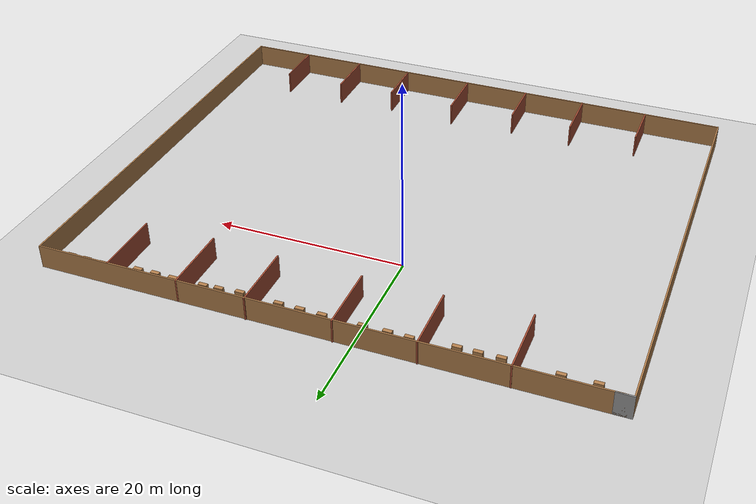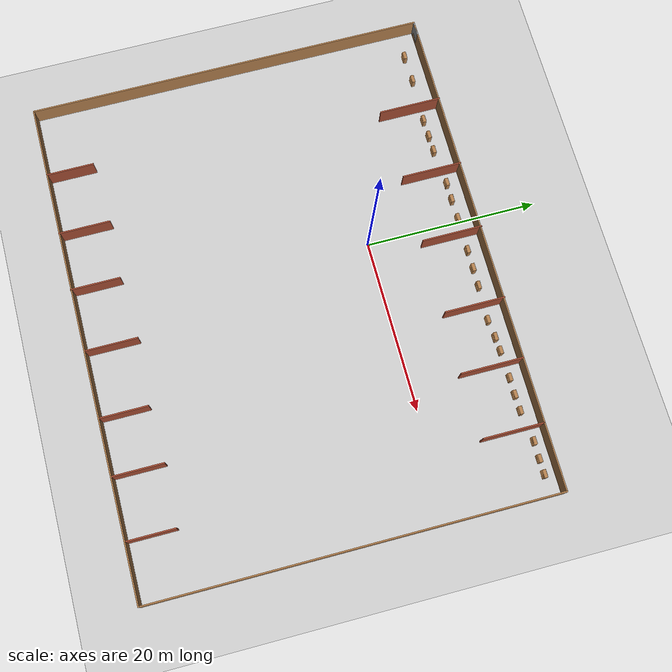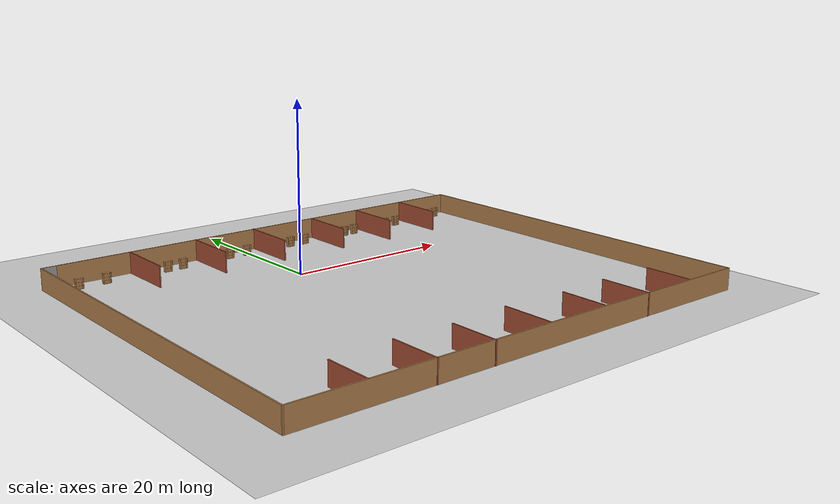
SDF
<sdf version="1.7">
 <world name="default">
  <light name="sun" type="directional">
   <pose>0 0 10 0 -0 0</pose>
   <diffuse>0.8 0.8 0.8 1</diffuse>
   <specular>0.2 0.2 0.2 1</specular>
   <attenuation>
    <range>1000</range>
    <constant>0.9</constant>
    <linear>0.01</linear>
    <quadratic>0.001</quadratic>
   </attenuation>
   <direction>-0.5 0.1 -0.9</direction>
   <spot><inner_angle>0</inner_angle><outer_angle>0</outer_angle><falloff>0</falloff></spot>
  </light>
  <model name="ground_plane">
   <static>1</static>
   <link name="link">
    <collision name="collision">
     <geometry><plane><normal>0 0 1</normal><size>100 100</size></plane></geometry>
     <surface><friction><ode><mu>100</mu><mu2>50</mu2></ode></friction></surface>
    </collision>
    <visual name="visual">
     <cast_shadows>0</cast_shadows>
     <geometry><plane><normal>0 0 1</normal><size>100 100</size></plane></geometry>
     <material>
      <script><uri>file://media/materials/scripts/gazebo.material</uri><name>Gazebo/Grey</name></script>
     </material>
    </visual>
   </link>
  </model>
  <gravity>0 0 -9.8</gravity>
  <magnetic_field>6e-06 2.3e-05 -4.2e-05</magnetic_field>
  <atmosphere type="adiabatic"/>
  <physics type="ode">
   <max_step_size>0.001</max_step_size>
   <real_time_factor>1</real_time_factor>
   <real_time_update_rate>1000</real_time_update_rate>
  </physics>
  <scene><ambient>0.4 0.4 0.4 1</ambient><background>0.7 0.7 0.7 1</background><shadows>1</shadows></scene>
  <audio><device>default</device></audio>
  <spherical_coordinates>
   <surface_model>EARTH_WGS84</surface_model>
   <latitude_deg>0</latitude_deg>
   <longitude_deg>0</longitude_deg>
   <elevation>0</elevation>
   <heading_deg>0</heading_deg>
  </spherical_coordinates>
  <model name="smart_factory">
   <pose>3.77458 -10.6449 0 0 -0 0</pose>
   <link name="Wall_0">
    <collision name="Wall_0_Collision">
     <geometry><box><size>57.5 0.15 2.5</size></box></geometry>
     <pose>0 0 1.25 0 -0 0</pose>
    </collision>
    <visual name="Wall_0_Visual">
     <pose>0 0 1.25 0 -0 0</pose>
     <geometry><box><size>57.5 0.15 2.5</size></box></geometry>
     <material>
      <script><uri>file://media/materials/scripts/gazebo.material</uri><name>Gazebo/Wood</name></script>
      <ambient>1 1 1 1</ambient>
     </material>
     <meta><layer>0</layer></meta>
    </visual>
    <pose>0.249999 23.2857 0 0 -0 0</pose>
   </link>
   <link name="Wall_1">
    <collision name="Wall_1_Collision">
     <geometry><box><size>46.75 0.15 2.5</size></box></geometry>
     <pose>0 0 1.25 0 -0 0</pose>
    </collision>
    <visual name="Wall_1_Visual">
     <pose>0 0 1.25 0 -0 0</pose>
     <geometry><box><size>46.75 0.15 2.5</size></box></geometry>
     <material>
      <script><uri>file://media/materials/scripts/gazebo.material</uri><name>Gazebo/Wood</name></script>
      <ambient>1 1 1 1</ambient>
     </material>
     <meta><layer>0</layer></meta>
    </visual>
    <pose>28.925 -0.014326 0 0 -0 -1.5708</pose>
   </link>
   <link name="Wall_17">
    <collision name="Wall_17_Collision">
     <geometry><box><size>7.25 0.15 2.5</size></box></geometry>
     <pose>0 0 1.25 0 -0 0</pose>
    </collision>
    <visual name="Wall_17_Visual">
     <pose>0 0 1.25 0 -0 0</pose>
     <geometry><box><size>7.25 0.15 2.5</size></box></geometry>
     <material>
      <script><uri>file://media/materials/scripts/gazebo.material</uri><name>Gazebo/Bricks</name></script>
      <ambient>1 1 1 1</ambient>
     </material>
     <meta><layer>0</layer></meta>
    </visual>
    <pose>-18.5075 19.7719 0 0 -0 1.5708</pose>
   </link>
   <link name="Wall_19">
    <collision name="Wall_19_Collision">
     <geometry><box><size>7 0.15 2.5</size></box></geometry>
     <pose>0 0 1.25 0 -0 0</pose>
    </collision>
    <visual name="Wall_19_Visual">
     <pose>0 0 1.25 0 -0 0</pose>
     <geometry><box><size>7 0.15 2.5</size></box></geometry>
     <material>
      <script><uri>file://media/materials/scripts/gazebo.material</uri><name>Gazebo/Bricks</name></script>
      <ambient>1 1 1 1</ambient>
     </material>
     <meta><layer>0</layer></meta>
    </visual>
    <pose>-10.0182 19.9528 0 0 -0 1.5708</pose>
   </link>
   <link name="Wall_2">
    <collision name="Wall_2_Collision">
     <geometry><box><size>58 0.15 2.5</size></box></geometry>
     <pose>0 0 1.25 0 -0 0</pose>
    </collision>
    <visual name="Wall_2_Visual">
     <pose>0 0 1.25 0 -0 0</pose>
     <geometry><box><size>58 0.15 2.5</size></box></geometry>
     <material>
      <script><uri>file://media/materials/scripts/gazebo.material</uri><name>Gazebo/Wood</name></script>
      <ambient>1 1 1 1</ambient>
     </material>
     <meta><layer>0</layer></meta>
    </visual>
    <pose>-1e-06 -23.3143 0 0 -0 3.14159</pose>
   </link>
   <link name="Wall_21">
    <collision name="Wall_21_Collision">
     <geometry><box><size>7 0.15 2.5</size></box></geometry>
     <pose>0 0 1.25 0 -0 0</pose>
    </collision>
    <visual name="Wall_21_Visual">
     <pose>0 0 1.25 0 -0 0</pose>
     <geometry><box><size>7 0.15 2.5</size></box></geometry>
     <material>
      <script><uri>file://media/materials/scripts/gazebo.material</uri><name>Gazebo/Bricks</name></script>
      <ambient>1 1 1 1</ambient>
     </material>
     <meta><layer>0</layer></meta>
    </visual>
    <pose>-1.95591 19.9528 0 0 -0 1.5708</pose>
   </link>
   <link name="Wall_23">
    <collision name="Wall_23_Collision">
     <geometry><box><size>7 0.15 2.5</size></box></geometry>
     <pose>0 0 1.25 0 -0 0</pose>
    </collision>
    <visual name="Wall_23_Visual">
     <pose>0 0 1.25 0 -0 0</pose>
     <geometry><box><size>7 0.15 2.5</size></box></geometry>
     <material>
      <script><uri>file://media/materials/scripts/gazebo.material</uri><name>Gazebo/Bricks</name></script>
      <ambient>1 1 1 1</ambient>
     </material>
     <meta><layer>0</layer></meta>
    </visual>
    <pose>6.74682 19.9528 0 0 -0 1.5708</pose>
   </link>
   <link name="Wall_25">
    <collision name="Wall_25_Collision">
     <geometry><box><size>7.25 0.15 2.5</size></box></geometry>
     <pose>0 0 1.25 0 -0 0</pose>
    </collision>
    <visual name="Wall_25_Visual">
     <pose>0 0 1.25 0 -0 0</pose>
     <geometry><box><size>7.25 0.15 2.5</size></box></geometry>
     <material>
      <script><uri>file://media/materials/scripts/gazebo.material</uri><name>Gazebo/Bricks</name></script>
      <ambient>1 1 1 1</ambient>
     </material>
     <meta><layer>0</layer></meta>
    </visual>
    <pose>13.8698 19.7505 0 0 -0 1.5708</pose>
   </link>
   <link name="Wall_27">
    <collision name="Wall_27_Collision">
     <geometry><box><size>7 0.15 2.5</size></box></geometry>
     <pose>0 0 1.25 0 -0 0</pose>
    </collision>
    <visual name="Wall_27_Visual">
     <pose>0 0 1.25 0 -0 0</pose>
     <geometry><box><size>7 0.15 2.5</size></box></geometry>
     <material>
      <script><uri>file://media/materials/scripts/gazebo.material</uri><name>Gazebo/Bricks</name></script>
      <ambient>1 1 1 1</ambient>
     </material>
     <meta><layer>0</layer></meta>
    </visual>
    <pose>21.313 19.8105 0 0 -0 1.5708</pose>
   </link>
   <link name="Wall_29">
    <collision name="Wall_29_Collision">
     <geometry><box><size>5.5 0.15 2.5</size></box></geometry>
     <pose>0 0 1.25 0 -0 0</pose>
    </collision>
    <visual name="Wall_29_Visual">
     <pose>0 0 1.25 0 -0 0</pose>
     <geometry><box><size>5.5 0.15 2.5</size></box></geometry>
     <material>
      <script><uri>file://media/materials/scripts/gazebo.material</uri><name>Gazebo/Bricks</name></script>
      <ambient>1 1 1 1</ambient>
     </material>
     <meta><layer>0</layer></meta>
    </visual>
    <pose>-20.6422 -20.5952 0 0 -0 -1.5708</pose>
   </link>
   <link name="Wall_3">
    <collision name="Wall_3_Collision">
     <geometry><box><size>46.75 0.15 2.5</size></box></geometry>
     <pose>0 0 1.25 0 -0 0</pose>
    </collision>
    <visual name="Wall_3_Visual">
     <pose>0 0 1.25 0 -0 0</pose>
     <geometry><box><size>46.75 0.15 2.5</size></box></geometry>
     <material>
      <script><uri>file://media/materials/scripts/gazebo.material</uri><name>Gazebo/Wood</name></script>
      <ambient>1 1 1 1</ambient>
     </material>
     <meta><layer>0</layer></meta>
    </visual>
    <pose>-28.925 -0.014326 0 0 -0 1.5708</pose>
   </link>
   <link name="Wall_31">
    <collision name="Wall_31_Collision">
     <geometry><box><size>6 0.15 2.5</size></box></geometry>
     <pose>0 0 1.25 0 -0 0</pose>
    </collision>
    <visual name="Wall_31_Visual">
     <pose>0 0 1.25 0 -0 0</pose>
     <geometry><box><size>6 0.15 2.5</size></box></geometry>
     <material>
      <script><uri>file://media/materials/scripts/gazebo.material</uri><name>Gazebo/Bricks</name></script>
      <ambient>1 1 1 1</ambient>
     </material>
     <meta><layer>0</layer></meta>
    </visual>
    <pose>-13.2417 -20.4182 0 0 -0 -1.5708</pose>
   </link>
   <link name="Wall_33">
    <collision name="Wall_33_Collision">
     <geometry><box><size>5.75 0.15 2.5</size></box></geometry>
     <pose>0 0 1.25 0 -0 0</pose>
    </collision>
    <visual name="Wall_33_Visual">
     <pose>0 0 1.25 0 -0 0</pose>
     <geometry><box><size>5.75 0.15 2.5</size></box></geometry>
     <material>
      <script><uri>file://media/materials/scripts/gazebo.material</uri><name>Gazebo/Bricks</name></script>
      <ambient>1 1 1 1</ambient>
     </material>
     <meta><layer>0</layer></meta>
    </visual>
    <pose>-6.34641 -20.5778 0 0 -0 -1.5708</pose>
   </link>
   <link name="Wall_35">
    <collision name="Wall_35_Collision">
     <geometry><box><size>6 0.15 2.5</size></box></geometry>
     <pose>0 0 1.25 0 -0 0</pose>
    </collision>
    <visual name="Wall_35_Visual">
     <pose>0 0 1.25 0 -0 0</pose>
     <geometry><box><size>6 0.15 2.5</size></box></geometry>
     <material>
      <script><uri>file://media/materials/scripts/gazebo.material</uri><name>Gazebo/Bricks</name></script>
      <ambient>1 1 1 1</ambient>
     </material>
     <meta><layer>0</layer></meta>
    </visual>
    <pose>0.947372 -20.2545 0 0 -0 -1.5708</pose>
   </link>
   <link name="Wall_37">
    <collision name="Wall_37_Collision">
     <geometry><box><size>5.5 0.15 2.5</size></box></geometry>
     <pose>0 0 1.25 0 -0 0</pose>
    </collision>
    <visual name="Wall_37_Visual">
     <pose>0 0 1.25 0 -0 0</pose>
     <geometry><box><size>5.5 0.15 2.5</size></box></geometry>
     <material>
      <script><uri>file://media/materials/scripts/gazebo.material</uri><name>Gazebo/Bricks</name></script>
      <ambient>1 1 1 1</ambient>
     </material>
     <meta><layer>0</layer></meta>
    </visual>
    <pose>8.67522 -20.4955 0 0 -0 -1.5708</pose>
   </link>
   <link name="Wall_39">
    <collision name="Wall_39_Collision">
     <geometry><box><size>6 0.15 2.5</size></box></geometry>
     <pose>0 0 1.25 0 -0 0</pose>
    </collision>
    <visual name="Wall_39_Visual">
     <pose>0 0 1.25 0 -0 0</pose>
     <geometry><box><size>6 0.15 2.5</size></box></geometry>
     <material>
      <script><uri>file://media/materials/scripts/gazebo.material</uri><name>Gazebo/Bricks</name></script>
      <ambient>1 1 1 1</ambient>
     </material>
     <meta><layer>0</layer></meta>
    </visual>
    <pose>15.1578 -20.4182 0 0 -0 -1.5708</pose>
   </link>
   <link name="Wall_4">
    <collision name="Wall_4_Collision">
     <geometry><box><size>1.75 0.15 2.5</size></box></geometry>
     <pose>0 0 1.25 0 -0 0</pose>
    </collision>
    <visual name="Wall_4_Visual">
     <pose>0 0 1.25 0 -0 0</pose>
     <geometry><box><size>1.75 0.15 2.5</size></box></geometry>
     <material>
      <script><uri>file://media/materials/scripts/gazebo.material</uri><name>Gazebo/Grey</name></script>
      <ambient>1 1 1 1</ambient>
     </material>
     <meta><layer>0</layer></meta>
    </visual>
    <pose>-28.125 23.2857 0 0 -0 0</pose>
   </link>
   <link name="Wall_41">
    <collision name="Wall_41_Collision">
     <geometry><box><size>5.5 0.15 2.5</size></box></geometry>
     <pose>0 0 1.25 0 -0 0</pose>
    </collision>
    <visual name="Wall_41_Visual">
     <pose>0 0 1.25 0 -0 0</pose>
     <geometry><box><size>5.5 0.15 2.5</size></box></geometry>
     <material>
      <script><uri>file://media/materials/scripts/gazebo.material</uri><name>Gazebo/Bricks</name></script>
      <ambient>1 1 1 1</ambient>
     </material>
     <meta><layer>0</layer></meta>
    </visual>
    <pose>22.1527 -20.4742 0 0 -0 -1.5708</pose>
   </link>
   <static>1</static>
  </model>
  <model name="bookshelf">
   <static>1</static>
   <link name="link">
    <inertial><mass>1</mass></inertial>
    <collision name="back">
     <pose>0 0.005 0.6 0 -0 0</pose>
     <geometry><box><size>0.9 0.01 1.2</size></box></geometry>
    </collision>
    <visual name="visual1">
     <pose>0 0.005 0.6 0 -0 0</pose>
     <geometry><box><size>0.9 0.01 1.2</size></box></geometry>
     <material>
      <script><uri>file://media/materials/scripts/gazebo.material</uri><name>Gazebo/Wood</name></script>
     </material>
    </visual>
    <collision name="left_side">
     <pose>0.45 -0.195 0.6 0 -0 0</pose>
     <geometry><box><size>0.02 0.4 1.2</size></box></geometry>
    </collision>
    <visual name="visual2">
     <pose>0.45 -0.195 0.6 0 -0 0</pose>
     <geometry><box><size>0.02 0.4 1.2</size></box></geometry>
     <material>
      <script><uri>file://media/materials/scripts/gazebo.material</uri><name>Gazebo/Wood</name></script>
     </material>
    </visual>
    <collision name="right_side">
     <pose>-0.45 -0.195 0.6 0 -0 0</pose>
     <geometry><box><size>0.02 0.4 1.2</size></box></geometry>
    </collision>
    <visual name="visual3">
     <pose>-0.45 -0.195 0.6 0 -0 0</pose>
     <geometry><box><size>0.02 0.4 1.2</size></box></geometry>
     <material>
      <script><uri>file://media/materials/scripts/gazebo.material</uri><name>Gazebo/Wood</name></script>
     </material>
    </visual>
    <collision name="bottom">
     <pose>0 -0.195 0.03 0 -0 0</pose>
     <geometry><box><size>0.88 0.4 0.06</size></box></geometry>
    </collision>
    <visual name="visual4">
     <pose>0 -0.195 0.03 0 -0 0</pose>
     <geometry><box><size>0.88 0.4 0.06</size></box></geometry>
     <material>
      <script><uri>file://media/materials/scripts/gazebo.material</uri><name>Gazebo/Wood</name></script>
     </material>
    </visual>
    <collision name="top">
     <pose>0 -0.195 1.19 0 -0 0</pose>
     <geometry><box><size>0.88 0.4 0.02</size></box></geometry>
    </collision>
    <visual name="visual5">
     <pose>0 -0.195 1.19 0 -0 0</pose>
     <geometry><box><size>0.88 0.4 0.02</size></box></geometry>
     <material>
      <script><uri>file://media/materials/scripts/gazebo.material</uri><name>Gazebo/Wood</name></script>
     </material>
    </visual>
    <collision name="low_shelf">
     <pose>0 -0.195 0.43 0 -0 0</pose>
     <geometry><box><size>0.88 0.4 0.02</size></box></geometry>
    </collision>
    <visual name="visual6">
     <pose>0 -0.195 0.43 0 -0 0</pose>
     <geometry><box><size>0.88 0.4 0.02</size></box></geometry>
     <material>
      <script><uri>file://media/materials/scripts/gazebo.material</uri><name>Gazebo/Wood</name></script>
     </material>
    </visual>
    <collision name="high_shelf">
     <pose>0 -0.195 0.8 0 -0 0</pose>
     <geometry><box><size>0.88 0.4 0.02</size></box></geometry>
    </collision>
    <visual name="visual7">
     <pose>0 -0.195 0.8 0 -0 0</pose>
     <geometry><box><size>0.88 0.4 0.02</size></box></geometry>
     <material>
      <script><uri>file://media/materials/scripts/gazebo.material</uri><name>Gazebo/Wood</name></script>
     </material>
    </visual>
   </link>
   <pose>-21.8442 10.8712 0 0 -0 0</pose>
  </model>
  <model name="bookshelf_0">
   <static>1</static>
   <link name="link">
    <inertial><mass>1</mass></inertial>
    <collision name="back">
     <pose>0 0.005 0.6 0 -0 0</pose>
     <geometry><box><size>0.9 0.01 1.2</size></box></geometry>
    </collision>
    <visual name="visual1">
     <pose>0 0.005 0.6 0 -0 0</pose>
     <geometry><box><size>0.9 0.01 1.2</size></box></geometry>
     <material>
      <script><uri>file://media/materials/scripts/gazebo.material</uri><name>Gazebo/Wood</name></script>
     </material>
    </visual>
    <collision name="left_side">
     <pose>0.45 -0.195 0.6 0 -0 0</pose>
     <geometry><box><size>0.02 0.4 1.2</size></box></geometry>
    </collision>
    <visual name="visual2">
     <pose>0.45 -0.195 0.6 0 -0 0</pose>
     <geometry><box><size>0.02 0.4 1.2</size></box></geometry>
     <material>
      <script><uri>file://media/materials/scripts/gazebo.material</uri><name>Gazebo/Wood</name></script>
     </material>
    </visual>
    <collision name="right_side">
     <pose>-0.45 -0.195 0.6 0 -0 0</pose>
     <geometry><box><size>0.02 0.4 1.2</size></box></geometry>
    </collision>
    <visual name="visual3">
     <pose>-0.45 -0.195 0.6 0 -0 0</pose>
     <geometry><box><size>0.02 0.4 1.2</size></box></geometry>
     <material>
      <script><uri>file://media/materials/scripts/gazebo.material</uri><name>Gazebo/Wood</name></script>
     </material>
    </visual>
    <collision name="bottom">
     <pose>0 -0.195 0.03 0 -0 0</pose>
     <geometry><box><size>0.88 0.4 0.06</size></box></geometry>
    </collision>
    <visual name="visual4">
     <pose>0 -0.195 0.03 0 -0 0</pose>
     <geometry><box><size>0.88 0.4 0.06</size></box></geometry>
     <material>
      <script><uri>file://media/materials/scripts/gazebo.material</uri><name>Gazebo/Wood</name></script>
     </material>
    </visual>
    <collision name="top">
     <pose>0 -0.195 1.19 0 -0 0</pose>
     <geometry><box><size>0.88 0.4 0.02</size></box></geometry>
    </collision>
    <visual name="visual5">
     <pose>0 -0.195 1.19 0 -0 0</pose>
     <geometry><box><size>0.88 0.4 0.02</size></box></geometry>
     <material>
      <script><uri>file://media/materials/scripts/gazebo.material</uri><name>Gazebo/Wood</name></script>
     </material>
    </visual>
    <collision name="low_shelf">
     <pose>0 -0.195 0.43 0 -0 0</pose>
     <geometry><box><size>0.88 0.4 0.02</size></box></geometry>
    </collision>
    <visual name="visual6">
     <pose>0 -0.195 0.43 0 -0 0</pose>
     <geometry><box><size>0.88 0.4 0.02</size></box></geometry>
     <material>
      <script><uri>file://media/materials/scripts/gazebo.material</uri><name>Gazebo/Wood</name></script>
     </material>
    </visual>
    <collision name="high_shelf">
     <pose>0 -0.195 0.8 0 -0 0</pose>
     <geometry><box><size>0.88 0.4 0.02</size></box></geometry>
    </collision>
    <visual name="visual7">
     <pose>0 -0.195 0.8 0 -0 0</pose>
     <geometry><box><size>0.88 0.4 0.02</size></box></geometry>
     <material>
      <script><uri>file://media/materials/scripts/gazebo.material</uri><name>Gazebo/Wood</name></script>
     </material>
    </visual>
   </link>
   <pose>-18.588 10.9215 0 0 -0 0</pose>
  </model>
  <model name="bookshelf_1">
   <static>1</static>
   <link name="link">
    <inertial><mass>1</mass></inertial>
    <collision name="back">
     <pose>0 0.005 0.6 0 -0 0</pose>
     <geometry><box><size>0.9 0.01 1.2</size></box></geometry>
    </collision>
    <visual name="visual1">
     <pose>0 0.005 0.6 0 -0 0</pose>
     <geometry><box><size>0.9 0.01 1.2</size></box></geometry>
     <material>
      <script><uri>file://media/materials/scripts/gazebo.material</uri><name>Gazebo/Wood</name></script>
     </material>
    </visual>
    <collision name="left_side">
     <pose>0.45 -0.195 0.6 0 -0 0</pose>
     <geometry><box><size>0.02 0.4 1.2</size></box></geometry>
    </collision>
    <visual name="visual2">
     <pose>0.45 -0.195 0.6 0 -0 0</pose>
     <geometry><box><size>0.02 0.4 1.2</size></box></geometry>
     <material>
      <script><uri>file://media/materials/scripts/gazebo.material</uri><name>Gazebo/Wood</name></script>
     </material>
    </visual>
    <collision name="right_side">
     <pose>-0.45 -0.195 0.6 0 -0 0</pose>
     <geometry><box><size>0.02 0.4 1.2</size></box></geometry>
    </collision>
    <visual name="visual3">
     <pose>-0.45 -0.195 0.6 0 -0 0</pose>
     <geometry><box><size>0.02 0.4 1.2</size></box></geometry>
     <material>
      <script><uri>file://media/materials/scripts/gazebo.material</uri><name>Gazebo/Wood</name></script>
     </material>
    </visual>
    <collision name="bottom">
     <pose>0 -0.195 0.03 0 -0 0</pose>
     <geometry><box><size>0.88 0.4 0.06</size></box></geometry>
    </collision>
    <visual name="visual4">
     <pose>0 -0.195 0.03 0 -0 0</pose>
     <geometry><box><size>0.88 0.4 0.06</size></box></geometry>
     <material>
      <script><uri>file://media/materials/scripts/gazebo.material</uri><name>Gazebo/Wood</name></script>
     </material>
    </visual>
    <collision name="top">
     <pose>0 -0.195 1.19 0 -0 0</pose>
     <geometry><box><size>0.88 0.4 0.02</size></box></geometry>
    </collision>
    <visual name="visual5">
     <pose>0 -0.195 1.19 0 -0 0</pose>
     <geometry><box><size>0.88 0.4 0.02</size></box></geometry>
     <material>
      <script><uri>file://media/materials/scripts/gazebo.material</uri><name>Gazebo/Wood</name></script>
     </material>
    </visual>
    <collision name="low_shelf">
     <pose>0 -0.195 0.43 0 -0 0</pose>
     <geometry><box><size>0.88 0.4 0.02</size></box></geometry>
    </collision>
    <visual name="visual6">
     <pose>0 -0.195 0.43 0 -0 0</pose>
     <geometry><box><size>0.88 0.4 0.02</size></box></geometry>
     <material>
      <script><uri>file://media/materials/scripts/gazebo.material</uri><name>Gazebo/Wood</name></script>
     </material>
    </visual>
    <collision name="high_shelf">
     <pose>0 -0.195 0.8 0 -0 0</pose>
     <geometry><box><size>0.88 0.4 0.02</size></box></geometry>
    </collision>
    <visual name="visual7">
     <pose>0 -0.195 0.8 0 -0 0</pose>
     <geometry><box><size>0.88 0.4 0.02</size></box></geometry>
     <material>
      <script><uri>file://media/materials/scripts/gazebo.material</uri><name>Gazebo/Wood</name></script>
     </material>
    </visual>
   </link>
   <pose>-13.2401 10.718 0 0 -0 0</pose>
  </model>
  <model name="bookshelf_2">
   <static>1</static>
   <link name="link">
    <inertial><mass>1</mass></inertial>
    <collision name="back">
     <pose>0 0.005 0.6 0 -0 0</pose>
     <geometry><box><size>0.9 0.01 1.2</size></box></geometry>
    </collision>
    <visual name="visual1">
     <pose>0 0.005 0.6 0 -0 0</pose>
     <geometry><box><size>0.9 0.01 1.2</size></box></geometry>
     <material>
      <script><uri>file://media/materials/scripts/gazebo.material</uri><name>Gazebo/Wood</name></script>
     </material>
    </visual>
    <collision name="left_side">
     <pose>0.45 -0.195 0.6 0 -0 0</pose>
     <geometry><box><size>0.02 0.4 1.2</size></box></geometry>
    </collision>
    <visual name="visual2">
     <pose>0.45 -0.195 0.6 0 -0 0</pose>
     <geometry><box><size>0.02 0.4 1.2</size></box></geometry>
     <material>
      <script><uri>file://media/materials/scripts/gazebo.material</uri><name>Gazebo/Wood</name></script>
     </material>
    </visual>
    <collision name="right_side">
     <pose>-0.45 -0.195 0.6 0 -0 0</pose>
     <geometry><box><size>0.02 0.4 1.2</size></box></geometry>
    </collision>
    <visual name="visual3">
     <pose>-0.45 -0.195 0.6 0 -0 0</pose>
     <geometry><box><size>0.02 0.4 1.2</size></box></geometry>
     <material>
      <script><uri>file://media/materials/scripts/gazebo.material</uri><name>Gazebo/Wood</name></script>
     </material>
    </visual>
    <collision name="bottom">
     <pose>0 -0.195 0.03 0 -0 0</pose>
     <geometry><box><size>0.88 0.4 0.06</size></box></geometry>
    </collision>
    <visual name="visual4">
     <pose>0 -0.195 0.03 0 -0 0</pose>
     <geometry><box><size>0.88 0.4 0.06</size></box></geometry>
     <material>
      <script><uri>file://media/materials/scripts/gazebo.material</uri><name>Gazebo/Wood</name></script>
     </material>
    </visual>
    <collision name="top">
     <pose>0 -0.195 1.19 0 -0 0</pose>
     <geometry><box><size>0.88 0.4 0.02</size></box></geometry>
    </collision>
    <visual name="visual5">
     <pose>0 -0.195 1.19 0 -0 0</pose>
     <geometry><box><size>0.88 0.4 0.02</size></box></geometry>
     <material>
      <script><uri>file://media/materials/scripts/gazebo.material</uri><name>Gazebo/Wood</name></script>
     </material>
    </visual>
    <collision name="low_shelf">
     <pose>0 -0.195 0.43 0 -0 0</pose>
     <geometry><box><size>0.88 0.4 0.02</size></box></geometry>
    </collision>
    <visual name="visual6">
     <pose>0 -0.195 0.43 0 -0 0</pose>
     <geometry><box><size>0.88 0.4 0.02</size></box></geometry>
     <material>
      <script><uri>file://media/materials/scripts/gazebo.material</uri><name>Gazebo/Wood</name></script>
     </material>
    </visual>
    <collision name="high_shelf">
     <pose>0 -0.195 0.8 0 -0 0</pose>
     <geometry><box><size>0.88 0.4 0.02</size></box></geometry>
    </collision>
    <visual name="visual7">
     <pose>0 -0.195 0.8 0 -0 0</pose>
     <geometry><box><size>0.88 0.4 0.02</size></box></geometry>
     <material>
      <script><uri>file://media/materials/scripts/gazebo.material</uri><name>Gazebo/Wood</name></script>
     </material>
    </visual>
   </link>
   <pose>-9.16775 10.7529 0 0 -0 0</pose>
  </model>
  <model name="bookshelf_3">
   <static>1</static>
   <link name="link">
    <inertial><mass>1</mass></inertial>
    <collision name="back">
     <pose>0 0.005 0.6 0 -0 0</pose>
     <geometry><box><size>0.9 0.01 1.2</size></box></geometry>
    </collision>
    <visual name="visual1">
     <pose>0 0.005 0.6 0 -0 0</pose>
     <geometry><box><size>0.9 0.01 1.2</size></box></geometry>
     <material>
      <script><uri>file://media/materials/scripts/gazebo.material</uri><name>Gazebo/Wood</name></script>
     </material>
    </visual>
    <collision name="left_side">
     <pose>0.45 -0.195 0.6 0 -0 0</pose>
     <geometry><box><size>0.02 0.4 1.2</size></box></geometry>
    </collision>
    <visual name="visual2">
     <pose>0.45 -0.195 0.6 0 -0 0</pose>
     <geometry><box><size>0.02 0.4 1.2</size></box></geometry>
     <material>
      <script><uri>file://media/materials/scripts/gazebo.material</uri><name>Gazebo/Wood</name></script>
     </material>
    </visual>
    <collision name="right_side">
     <pose>-0.45 -0.195 0.6 0 -0 0</pose>
     <geometry><box><size>0.02 0.4 1.2</size></box></geometry>
    </collision>
    <visual name="visual3">
     <pose>-0.45 -0.195 0.6 0 -0 0</pose>
     <geometry><box><size>0.02 0.4 1.2</size></box></geometry>
     <material>
      <script><uri>file://media/materials/scripts/gazebo.material</uri><name>Gazebo/Wood</name></script>
     </material>
    </visual>
    <collision name="bottom">
     <pose>0 -0.195 0.03 0 -0 0</pose>
     <geometry><box><size>0.88 0.4 0.06</size></box></geometry>
    </collision>
    <visual name="visual4">
     <pose>0 -0.195 0.03 0 -0 0</pose>
     <geometry><box><size>0.88 0.4 0.06</size></box></geometry>
     <material>
      <script><uri>file://media/materials/scripts/gazebo.material</uri><name>Gazebo/Wood</name></script>
     </material>
    </visual>
    <collision name="top">
     <pose>0 -0.195 1.19 0 -0 0</pose>
     <geometry><box><size>0.88 0.4 0.02</size></box></geometry>
    </collision>
    <visual name="visual5">
     <pose>0 -0.195 1.19 0 -0 0</pose>
     <geometry><box><size>0.88 0.4 0.02</size></box></geometry>
     <material>
      <script><uri>file://media/materials/scripts/gazebo.material</uri><name>Gazebo/Wood</name></script>
     </material>
    </visual>
    <collision name="low_shelf">
     <pose>0 -0.195 0.43 0 -0 0</pose>
     <geometry><box><size>0.88 0.4 0.02</size></box></geometry>
    </collision>
    <visual name="visual6">
     <pose>0 -0.195 0.43 0 -0 0</pose>
     <geometry><box><size>0.88 0.4 0.02</size></box></geometry>
     <material>
      <script><uri>file://media/materials/scripts/gazebo.material</uri><name>Gazebo/Wood</name></script>
     </material>
    </visual>
    <collision name="high_shelf">
     <pose>0 -0.195 0.8 0 -0 0</pose>
     <geometry><box><size>0.88 0.4 0.02</size></box></geometry>
    </collision>
    <visual name="visual7">
     <pose>0 -0.195 0.8 0 -0 0</pose>
     <geometry><box><size>0.88 0.4 0.02</size></box></geometry>
     <material>
      <script><uri>file://media/materials/scripts/gazebo.material</uri><name>Gazebo/Wood</name></script>
     </material>
    </visual>
   </link>
   <pose>-4.82056 11.062 0 0 -0 0</pose>
  </model>
  <model name="bookshelf_4">
   <static>1</static>
   <link name="link">
    <inertial><mass>1</mass></inertial>
    <collision name="back">
     <pose>0 0.005 0.6 0 -0 0</pose>
     <geometry><box><size>0.9 0.01 1.2</size></box></geometry>
    </collision>
    <visual name="visual1">
     <pose>0 0.005 0.6 0 -0 0</pose>
     <geometry><box><size>0.9 0.01 1.2</size></box></geometry>
     <material>
      <script><uri>file://media/materials/scripts/gazebo.material</uri><name>Gazebo/Wood</name></script>
     </material>
    </visual>
    <collision name="left_side">
     <pose>0.45 -0.195 0.6 0 -0 0</pose>
     <geometry><box><size>0.02 0.4 1.2</size></box></geometry>
    </collision>
    <visual name="visual2">
     <pose>0.45 -0.195 0.6 0 -0 0</pose>
     <geometry><box><size>0.02 0.4 1.2</size></box></geometry>
     <material>
      <script><uri>file://media/materials/scripts/gazebo.material</uri><name>Gazebo/Wood</name></script>
     </material>
    </visual>
    <collision name="right_side">
     <pose>-0.45 -0.195 0.6 0 -0 0</pose>
     <geometry><box><size>0.02 0.4 1.2</size></box></geometry>
    </collision>
    <visual name="visual3">
     <pose>-0.45 -0.195 0.6 0 -0 0</pose>
     <geometry><box><size>0.02 0.4 1.2</size></box></geometry>
     <material>
      <script><uri>file://media/materials/scripts/gazebo.material</uri><name>Gazebo/Wood</name></script>
     </material>
    </visual>
    <collision name="bottom">
     <pose>0 -0.195 0.03 0 -0 0</pose>
     <geometry><box><size>0.88 0.4 0.06</size></box></geometry>
    </collision>
    <visual name="visual4">
     <pose>0 -0.195 0.03 0 -0 0</pose>
     <geometry><box><size>0.88 0.4 0.06</size></box></geometry>
     <material>
      <script><uri>file://media/materials/scripts/gazebo.material</uri><name>Gazebo/Wood</name></script>
     </material>
    </visual>
    <collision name="top">
     <pose>0 -0.195 1.19 0 -0 0</pose>
     <geometry><box><size>0.88 0.4 0.02</size></box></geometry>
    </collision>
    <visual name="visual5">
     <pose>0 -0.195 1.19 0 -0 0</pose>
     <geometry><box><size>0.88 0.4 0.02</size></box></geometry>
     <material>
      <script><uri>file://media/materials/scripts/gazebo.material</uri><name>Gazebo/Wood</name></script>
     </material>
    </visual>
    <collision name="low_shelf">
     <pose>0 -0.195 0.43 0 -0 0</pose>
     <geometry><box><size>0.88 0.4 0.02</size></box></geometry>
    </collision>
    <visual name="visual6">
     <pose>0 -0.195 0.43 0 -0 0</pose>
     <geometry><box><size>0.88 0.4 0.02</size></box></geometry>
     <material>
      <script><uri>file://media/materials/scripts/gazebo.material</uri><name>Gazebo/Wood</name></script>
     </material>
    </visual>
    <collision name="high_shelf">
     <pose>0 -0.195 0.8 0 -0 0</pose>
     <geometry><box><size>0.88 0.4 0.02</size></box></geometry>
    </collision>
    <visual name="visual7">
     <pose>0 -0.195 0.8 0 -0 0</pose>
     <geometry><box><size>0.88 0.4 0.02</size></box></geometry>
     <material>
      <script><uri>file://media/materials/scripts/gazebo.material</uri><name>Gazebo/Wood</name></script>
     </material>
    </visual>
   </link>
   <pose>-0.324653 11.0459 0 0 -0 0</pose>
  </model>
  <model name="bookshelf_5">
   <static>1</static>
   <link name="link">
    <inertial><mass>1</mass></inertial>
    <collision name="back">
     <pose>0 0.005 0.6 0 -0 0</pose>
     <geometry><box><size>0.9 0.01 1.2</size></box></geometry>
    </collision>
    <visual name="visual1">
     <pose>0 0.005 0.6 0 -0 0</pose>
     <geometry><box><size>0.9 0.01 1.2</size></box></geometry>
     <material>
      <script><uri>file://media/materials/scripts/gazebo.material</uri><name>Gazebo/Wood</name></script>
     </material>
    </visual>
    <collision name="left_side">
     <pose>0.45 -0.195 0.6 0 -0 0</pose>
     <geometry><box><size>0.02 0.4 1.2</size></box></geometry>
    </collision>
    <visual name="visual2">
     <pose>0.45 -0.195 0.6 0 -0 0</pose>
     <geometry><box><size>0.02 0.4 1.2</size></box></geometry>
     <material>
      <script><uri>file://media/materials/scripts/gazebo.material</uri><name>Gazebo/Wood</name></script>
     </material>
    </visual>
    <collision name="right_side">
     <pose>-0.45 -0.195 0.6 0 -0 0</pose>
     <geometry><box><size>0.02 0.4 1.2</size></box></geometry>
    </collision>
    <visual name="visual3">
     <pose>-0.45 -0.195 0.6 0 -0 0</pose>
     <geometry><box><size>0.02 0.4 1.2</size></box></geometry>
     <material>
      <script><uri>file://media/materials/scripts/gazebo.material</uri><name>Gazebo/Wood</name></script>
     </material>
    </visual>
    <collision name="bottom">
     <pose>0 -0.195 0.03 0 -0 0</pose>
     <geometry><box><size>0.88 0.4 0.06</size></box></geometry>
    </collision>
    <visual name="visual4">
     <pose>0 -0.195 0.03 0 -0 0</pose>
     <geometry><box><size>0.88 0.4 0.06</size></box></geometry>
     <material>
      <script><uri>file://media/materials/scripts/gazebo.material</uri><name>Gazebo/Wood</name></script>
     </material>
    </visual>
    <collision name="top">
     <pose>0 -0.195 1.19 0 -0 0</pose>
     <geometry><box><size>0.88 0.4 0.02</size></box></geometry>
    </collision>
    <visual name="visual5">
     <pose>0 -0.195 1.19 0 -0 0</pose>
     <geometry><box><size>0.88 0.4 0.02</size></box></geometry>
     <material>
      <script><uri>file://media/materials/scripts/gazebo.material</uri><name>Gazebo/Wood</name></script>
     </material>
    </visual>
    <collision name="low_shelf">
     <pose>0 -0.195 0.43 0 -0 0</pose>
     <geometry><box><size>0.88 0.4 0.02</size></box></geometry>
    </collision>
    <visual name="visual6">
     <pose>0 -0.195 0.43 0 -0 0</pose>
     <geometry><box><size>0.88 0.4 0.02</size></box></geometry>
     <material>
      <script><uri>file://media/materials/scripts/gazebo.material</uri><name>Gazebo/Wood</name></script>
     </material>
    </visual>
    <collision name="high_shelf">
     <pose>0 -0.195 0.8 0 -0 0</pose>
     <geometry><box><size>0.88 0.4 0.02</size></box></geometry>
    </collision>
    <visual name="visual7">
     <pose>0 -0.195 0.8 0 -0 0</pose>
     <geometry><box><size>0.88 0.4 0.02</size></box></geometry>
     <material>
      <script><uri>file://media/materials/scripts/gazebo.material</uri><name>Gazebo/Wood</name></script>
     </material>
    </visual>
   </link>
   <pose>3.70248 10.9976 0 0 -0 0</pose>
  </model>
  <model name="bookshelf_6">
   <static>1</static>
   <link name="link">
    <inertial><mass>1</mass></inertial>
    <collision name="back">
     <pose>0 0.005 0.6 0 -0 0</pose>
     <geometry><box><size>0.9 0.01 1.2</size></box></geometry>
    </collision>
    <visual name="visual1">
     <pose>0 0.005 0.6 0 -0 0</pose>
     <geometry><box><size>0.9 0.01 1.2</size></box></geometry>
     <material>
      <script><uri>file://media/materials/scripts/gazebo.material</uri><name>Gazebo/Wood</name></script>
     </material>
    </visual>
    <collision name="left_side">
     <pose>0.45 -0.195 0.6 0 -0 0</pose>
     <geometry><box><size>0.02 0.4 1.2</size></box></geometry>
    </collision>
    <visual name="visual2">
     <pose>0.45 -0.195 0.6 0 -0 0</pose>
     <geometry><box><size>0.02 0.4 1.2</size></box></geometry>
     <material>
      <script><uri>file://media/materials/scripts/gazebo.material</uri><name>Gazebo/Wood</name></script>
     </material>
    </visual>
    <collision name="right_side">
     <pose>-0.45 -0.195 0.6 0 -0 0</pose>
     <geometry><box><size>0.02 0.4 1.2</size></box></geometry>
    </collision>
    <visual name="visual3">
     <pose>-0.45 -0.195 0.6 0 -0 0</pose>
     <geometry><box><size>0.02 0.4 1.2</size></box></geometry>
     <material>
      <script><uri>file://media/materials/scripts/gazebo.material</uri><name>Gazebo/Wood</name></script>
     </material>
    </visual>
    <collision name="bottom">
     <pose>0 -0.195 0.03 0 -0 0</pose>
     <geometry><box><size>0.88 0.4 0.06</size></box></geometry>
    </collision>
    <visual name="visual4">
     <pose>0 -0.195 0.03 0 -0 0</pose>
     <geometry><box><size>0.88 0.4 0.06</size></box></geometry>
     <material>
      <script><uri>file://media/materials/scripts/gazebo.material</uri><name>Gazebo/Wood</name></script>
     </material>
    </visual>
    <collision name="top">
     <pose>0 -0.195 1.19 0 -0 0</pose>
     <geometry><box><size>0.88 0.4 0.02</size></box></geometry>
    </collision>
    <visual name="visual5">
     <pose>0 -0.195 1.19 0 -0 0</pose>
     <geometry><box><size>0.88 0.4 0.02</size></box></geometry>
     <material>
      <script><uri>file://media/materials/scripts/gazebo.material</uri><name>Gazebo/Wood</name></script>
     </material>
    </visual>
    <collision name="low_shelf">
     <pose>0 -0.195 0.43 0 -0 0</pose>
     <geometry><box><size>0.88 0.4 0.02</size></box></geometry>
    </collision>
    <visual name="visual6">
     <pose>0 -0.195 0.43 0 -0 0</pose>
     <geometry><box><size>0.88 0.4 0.02</size></box></geometry>
     <material>
      <script><uri>file://media/materials/scripts/gazebo.material</uri><name>Gazebo/Wood</name></script>
     </material>
    </visual>
    <collision name="high_shelf">
     <pose>0 -0.195 0.8 0 -0 0</pose>
     <geometry><box><size>0.88 0.4 0.02</size></box></geometry>
    </collision>
    <visual name="visual7">
     <pose>0 -0.195 0.8 0 -0 0</pose>
     <geometry><box><size>0.88 0.4 0.02</size></box></geometry>
     <material>
      <script><uri>file://media/materials/scripts/gazebo.material</uri><name>Gazebo/Wood</name></script>
     </material>
    </visual>
   </link>
   <pose>8.10292 10.9247 0 0 -0 0</pose>
  </model>
  <model name="bookshelf_7">
   <static>1</static>
   <link name="link">
    <inertial><mass>1</mass></inertial>
    <collision name="back">
     <pose>0 0.005 0.6 0 -0 0</pose>
     <geometry><box><size>0.9 0.01 1.2</size></box></geometry>
    </collision>
    <visual name="visual1">
     <pose>0 0.005 0.6 0 -0 0</pose>
     <geometry><box><size>0.9 0.01 1.2</size></box></geometry>
     <material>
      <script><uri>file://media/materials/scripts/gazebo.material</uri><name>Gazebo/Wood</name></script>
     </material>
    </visual>
    <collision name="left_side">
     <pose>0.45 -0.195 0.6 0 -0 0</pose>
     <geometry><box><size>0.02 0.4 1.2</size></box></geometry>
    </collision>
    <visual name="visual2">
     <pose>0.45 -0.195 0.6 0 -0 0</pose>
     <geometry><box><size>0.02 0.4 1.2</size></box></geometry>
     <material>
      <script><uri>file://media/materials/scripts/gazebo.material</uri><name>Gazebo/Wood</name></script>
     </material>
    </visual>
    <collision name="right_side">
     <pose>-0.45 -0.195 0.6 0 -0 0</pose>
     <geometry><box><size>0.02 0.4 1.2</size></box></geometry>
    </collision>
    <visual name="visual3">
     <pose>-0.45 -0.195 0.6 0 -0 0</pose>
     <geometry><box><size>0.02 0.4 1.2</size></box></geometry>
     <material>
      <script><uri>file://media/materials/scripts/gazebo.material</uri><name>Gazebo/Wood</name></script>
     </material>
    </visual>
    <collision name="bottom">
     <pose>0 -0.195 0.03 0 -0 0</pose>
     <geometry><box><size>0.88 0.4 0.06</size></box></geometry>
    </collision>
    <visual name="visual4">
     <pose>0 -0.195 0.03 0 -0 0</pose>
     <geometry><box><size>0.88 0.4 0.06</size></box></geometry>
     <material>
      <script><uri>file://media/materials/scripts/gazebo.material</uri><name>Gazebo/Wood</name></script>
     </material>
    </visual>
    <collision name="top">
     <pose>0 -0.195 1.19 0 -0 0</pose>
     <geometry><box><size>0.88 0.4 0.02</size></box></geometry>
    </collision>
    <visual name="visual5">
     <pose>0 -0.195 1.19 0 -0 0</pose>
     <geometry><box><size>0.88 0.4 0.02</size></box></geometry>
     <material>
      <script><uri>file://media/materials/scripts/gazebo.material</uri><name>Gazebo/Wood</name></script>
     </material>
    </visual>
    <collision name="low_shelf">
     <pose>0 -0.195 0.43 0 -0 0</pose>
     <geometry><box><size>0.88 0.4 0.02</size></box></geometry>
    </collision>
    <visual name="visual6">
     <pose>0 -0.195 0.43 0 -0 0</pose>
     <geometry><box><size>0.88 0.4 0.02</size></box></geometry>
     <material>
      <script><uri>file://media/materials/scripts/gazebo.material</uri><name>Gazebo/Wood</name></script>
     </material>
    </visual>
    <collision name="high_shelf">
     <pose>0 -0.195 0.8 0 -0 0</pose>
     <geometry><box><size>0.88 0.4 0.02</size></box></geometry>
    </collision>
    <visual name="visual7">
     <pose>0 -0.195 0.8 0 -0 0</pose>
     <geometry><box><size>0.88 0.4 0.02</size></box></geometry>
     <material>
      <script><uri>file://media/materials/scripts/gazebo.material</uri><name>Gazebo/Wood</name></script>
     </material>
    </visual>
   </link>
   <pose>12.2017 10.7548 0 0 -0 0</pose>
  </model>
  <model name="bookshelf_8">
   <static>1</static>
   <link name="link">
    <inertial><mass>1</mass></inertial>
    <collision name="back">
     <pose>0 0.005 0.6 0 -0 0</pose>
     <geometry><box><size>0.9 0.01 1.2</size></box></geometry>
    </collision>
    <visual name="visual1">
     <pose>0 0.005 0.6 0 -0 0</pose>
     <geometry><box><size>0.9 0.01 1.2</size></box></geometry>
     <material>
      <script><uri>file://media/materials/scripts/gazebo.material</uri><name>Gazebo/Wood</name></script>
     </material>
    </visual>
    <collision name="left_side">
     <pose>0.45 -0.195 0.6 0 -0 0</pose>
     <geometry><box><size>0.02 0.4 1.2</size></box></geometry>
    </collision>
    <visual name="visual2">
     <pose>0.45 -0.195 0.6 0 -0 0</pose>
     <geometry><box><size>0.02 0.4 1.2</size></box></geometry>
     <material>
      <script><uri>file://media/materials/scripts/gazebo.material</uri><name>Gazebo/Wood</name></script>
     </material>
    </visual>
    <collision name="right_side">
     <pose>-0.45 -0.195 0.6 0 -0 0</pose>
     <geometry><box><size>0.02 0.4 1.2</size></box></geometry>
    </collision>
    <visual name="visual3">
     <pose>-0.45 -0.195 0.6 0 -0 0</pose>
     <geometry><box><size>0.02 0.4 1.2</size></box></geometry>
     <material>
      <script><uri>file://media/materials/scripts/gazebo.material</uri><name>Gazebo/Wood</name></script>
     </material>
    </visual>
    <collision name="bottom">
     <pose>0 -0.195 0.03 0 -0 0</pose>
     <geometry><box><size>0.88 0.4 0.06</size></box></geometry>
    </collision>
    <visual name="visual4">
     <pose>0 -0.195 0.03 0 -0 0</pose>
     <geometry><box><size>0.88 0.4 0.06</size></box></geometry>
     <material>
      <script><uri>file://media/materials/scripts/gazebo.material</uri><name>Gazebo/Wood</name></script>
     </material>
    </visual>
    <collision name="top">
     <pose>0 -0.195 1.19 0 -0 0</pose>
     <geometry><box><size>0.88 0.4 0.02</size></box></geometry>
    </collision>
    <visual name="visual5">
     <pose>0 -0.195 1.19 0 -0 0</pose>
     <geometry><box><size>0.88 0.4 0.02</size></box></geometry>
     <material>
      <script><uri>file://media/materials/scripts/gazebo.material</uri><name>Gazebo/Wood</name></script>
     </material>
    </visual>
    <collision name="low_shelf">
     <pose>0 -0.195 0.43 0 -0 0</pose>
     <geometry><box><size>0.88 0.4 0.02</size></box></geometry>
    </collision>
    <visual name="visual6">
     <pose>0 -0.195 0.43 0 -0 0</pose>
     <geometry><box><size>0.88 0.4 0.02</size></box></geometry>
     <material>
      <script><uri>file://media/materials/scripts/gazebo.material</uri><name>Gazebo/Wood</name></script>
     </material>
    </visual>
    <collision name="high_shelf">
     <pose>0 -0.195 0.8 0 -0 0</pose>
     <geometry><box><size>0.88 0.4 0.02</size></box></geometry>
    </collision>
    <visual name="visual7">
     <pose>0 -0.195 0.8 0 -0 0</pose>
     <geometry><box><size>0.88 0.4 0.02</size></box></geometry>
     <material>
      <script><uri>file://media/materials/scripts/gazebo.material</uri><name>Gazebo/Wood</name></script>
     </material>
    </visual>
   </link>
   <pose>15.9545 11.0352 0 0 -0 0</pose>
  </model>
  <model name="bookshelf_9">
   <static>1</static>
   <link name="link">
    <inertial><mass>1</mass></inertial>
    <collision name="back">
     <pose>0 0.005 0.6 0 -0 0</pose>
     <geometry><box><size>0.9 0.01 1.2</size></box></geometry>
    </collision>
    <visual name="visual1">
     <pose>0 0.005 0.6 0 -0 0</pose>
     <geometry><box><size>0.9 0.01 1.2</size></box></geometry>
     <material>
      <script><uri>file://media/materials/scripts/gazebo.material</uri><name>Gazebo/Wood</name></script>
     </material>
    </visual>
    <collision name="left_side">
     <pose>0.45 -0.195 0.6 0 -0 0</pose>
     <geometry><box><size>0.02 0.4 1.2</size></box></geometry>
    </collision>
    <visual name="visual2">
     <pose>0.45 -0.195 0.6 0 -0 0</pose>
     <geometry><box><size>0.02 0.4 1.2</size></box></geometry>
     <material>
      <script><uri>file://media/materials/scripts/gazebo.material</uri><name>Gazebo/Wood</name></script>
     </material>
    </visual>
    <collision name="right_side">
     <pose>-0.45 -0.195 0.6 0 -0 0</pose>
     <geometry><box><size>0.02 0.4 1.2</size></box></geometry>
    </collision>
    <visual name="visual3">
     <pose>-0.45 -0.195 0.6 0 -0 0</pose>
     <geometry><box><size>0.02 0.4 1.2</size></box></geometry>
     <material>
      <script><uri>file://media/materials/scripts/gazebo.material</uri><name>Gazebo/Wood</name></script>
     </material>
    </visual>
    <collision name="bottom">
     <pose>0 -0.195 0.03 0 -0 0</pose>
     <geometry><box><size>0.88 0.4 0.06</size></box></geometry>
    </collision>
    <visual name="visual4">
     <pose>0 -0.195 0.03 0 -0 0</pose>
     <geometry><box><size>0.88 0.4 0.06</size></box></geometry>
     <material>
      <script><uri>file://media/materials/scripts/gazebo.material</uri><name>Gazebo/Wood</name></script>
     </material>
    </visual>
    <collision name="top">
     <pose>0 -0.195 1.19 0 -0 0</pose>
     <geometry><box><size>0.88 0.4 0.02</size></box></geometry>
    </collision>
    <visual name="visual5">
     <pose>0 -0.195 1.19 0 -0 0</pose>
     <geometry><box><size>0.88 0.4 0.02</size></box></geometry>
     <material>
      <script><uri>file://media/materials/scripts/gazebo.material</uri><name>Gazebo/Wood</name></script>
     </material>
    </visual>
    <collision name="low_shelf">
     <pose>0 -0.195 0.43 0 -0 0</pose>
     <geometry><box><size>0.88 0.4 0.02</size></box></geometry>
    </collision>
    <visual name="visual6">
     <pose>0 -0.195 0.43 0 -0 0</pose>
     <geometry><box><size>0.88 0.4 0.02</size></box></geometry>
     <material>
      <script><uri>file://media/materials/scripts/gazebo.material</uri><name>Gazebo/Wood</name></script>
     </material>
    </visual>
    <collision name="high_shelf">
     <pose>0 -0.195 0.8 0 -0 0</pose>
     <geometry><box><size>0.88 0.4 0.02</size></box></geometry>
    </collision>
    <visual name="visual7">
     <pose>0 -0.195 0.8 0 -0 0</pose>
     <geometry><box><size>0.88 0.4 0.02</size></box></geometry>
     <material>
      <script><uri>file://media/materials/scripts/gazebo.material</uri><name>Gazebo/Wood</name></script>
     </material>
    </visual>
   </link>
   <pose>19.1556 11.1082 0 0 -0 0</pose>
  </model>
  <model name="bookshelf_10">
   <static>1</static>
   <link name="link">
    <inertial><mass>1</mass></inertial>
    <collision name="back">
     <pose>0 0.005 0.6 0 -0 0</pose>
     <geometry><box><size>0.9 0.01 1.2</size></box></geometry>
    </collision>
    <visual name="visual1">
     <pose>0 0.005 0.6 0 -0 0</pose>
     <geometry><box><size>0.9 0.01 1.2</size></box></geometry>
     <material>
      <script><uri>file://media/materials/scripts/gazebo.material</uri><name>Gazebo/Wood</name></script>
     </material>
    </visual>
    <collision name="left_side">
     <pose>0.45 -0.195 0.6 0 -0 0</pose>
     <geometry><box><size>0.02 0.4 1.2</size></box></geometry>
    </collision>
    <visual name="visual2">
     <pose>0.45 -0.195 0.6 0 -0 0</pose>
     <geometry><box><size>0.02 0.4 1.2</size></box></geometry>
     <material>
      <script><uri>file://media/materials/scripts/gazebo.material</uri><name>Gazebo/Wood</name></script>
     </material>
    </visual>
    <collision name="right_side">
     <pose>-0.45 -0.195 0.6 0 -0 0</pose>
     <geometry><box><size>0.02 0.4 1.2</size></box></geometry>
    </collision>
    <visual name="visual3">
     <pose>-0.45 -0.195 0.6 0 -0 0</pose>
     <geometry><box><size>0.02 0.4 1.2</size></box></geometry>
     <material>
      <script><uri>file://media/materials/scripts/gazebo.material</uri><name>Gazebo/Wood</name></script>
     </material>
    </visual>
    <collision name="bottom">
     <pose>0 -0.195 0.03 0 -0 0</pose>
     <geometry><box><size>0.88 0.4 0.06</size></box></geometry>
    </collision>
    <visual name="visual4">
     <pose>0 -0.195 0.03 0 -0 0</pose>
     <geometry><box><size>0.88 0.4 0.06</size></box></geometry>
     <material>
      <script><uri>file://media/materials/scripts/gazebo.material</uri><name>Gazebo/Wood</name></script>
     </material>
    </visual>
    <collision name="top">
     <pose>0 -0.195 1.19 0 -0 0</pose>
     <geometry><box><size>0.88 0.4 0.02</size></box></geometry>
    </collision>
    <visual name="visual5">
     <pose>0 -0.195 1.19 0 -0 0</pose>
     <geometry><box><size>0.88 0.4 0.02</size></box></geometry>
     <material>
      <script><uri>file://media/materials/scripts/gazebo.material</uri><name>Gazebo/Wood</name></script>
     </material>
    </visual>
    <collision name="low_shelf">
     <pose>0 -0.195 0.43 0 -0 0</pose>
     <geometry><box><size>0.88 0.4 0.02</size></box></geometry>
    </collision>
    <visual name="visual6">
     <pose>0 -0.195 0.43 0 -0 0</pose>
     <geometry><box><size>0.88 0.4 0.02</size></box></geometry>
     <material>
      <script><uri>file://media/materials/scripts/gazebo.material</uri><name>Gazebo/Wood</name></script>
     </material>
    </visual>
    <collision name="high_shelf">
     <pose>0 -0.195 0.8 0 -0 0</pose>
     <geometry><box><size>0.88 0.4 0.02</size></box></geometry>
    </collision>
    <visual name="visual7">
     <pose>0 -0.195 0.8 0 -0 0</pose>
     <geometry><box><size>0.88 0.4 0.02</size></box></geometry>
     <material>
      <script><uri>file://media/materials/scripts/gazebo.material</uri><name>Gazebo/Wood</name></script>
     </material>
    </visual>
   </link>
   <pose>22.9811 11.1093 0 0 -0 0</pose>
  </model>
  <model name="bookshelf_11">
   <static>1</static>
   <link name="link">
    <inertial><mass>1</mass></inertial>
    <collision name="back">
     <pose>0 0.005 0.6 0 -0 0</pose>
     <geometry><box><size>0.9 0.01 1.2</size></box></geometry>
    </collision>
    <visual name="visual1">
     <pose>0 0.005 0.6 0 -0 0</pose>
     <geometry><box><size>0.9 0.01 1.2</size></box></geometry>
     <material>
      <script><uri>file://media/materials/scripts/gazebo.material</uri><name>Gazebo/Wood</name></script>
     </material>
    </visual>
    <collision name="left_side">
     <pose>0.45 -0.195 0.6 0 -0 0</pose>
     <geometry><box><size>0.02 0.4 1.2</size></box></geometry>
    </collision>
    <visual name="visual2">
     <pose>0.45 -0.195 0.6 0 -0 0</pose>
     <geometry><box><size>0.02 0.4 1.2</size></box></geometry>
     <material>
      <script><uri>file://media/materials/scripts/gazebo.material</uri><name>Gazebo/Wood</name></script>
     </material>
    </visual>
    <collision name="right_side">
     <pose>-0.45 -0.195 0.6 0 -0 0</pose>
     <geometry><box><size>0.02 0.4 1.2</size></box></geometry>
    </collision>
    <visual name="visual3">
     <pose>-0.45 -0.195 0.6 0 -0 0</pose>
     <geometry><box><size>0.02 0.4 1.2</size></box></geometry>
     <material>
      <script><uri>file://media/materials/scripts/gazebo.material</uri><name>Gazebo/Wood</name></script>
     </material>
    </visual>
    <collision name="bottom">
     <pose>0 -0.195 0.03 0 -0 0</pose>
     <geometry><box><size>0.88 0.4 0.06</size></box></geometry>
    </collision>
    <visual name="visual4">
     <pose>0 -0.195 0.03 0 -0 0</pose>
     <geometry><box><size>0.88 0.4 0.06</size></box></geometry>
     <material>
      <script><uri>file://media/materials/scripts/gazebo.material</uri><name>Gazebo/Wood</name></script>
     </material>
    </visual>
    <collision name="top">
     <pose>0 -0.195 1.19 0 -0 0</pose>
     <geometry><box><size>0.88 0.4 0.02</size></box></geometry>
    </collision>
    <visual name="visual5">
     <pose>0 -0.195 1.19 0 -0 0</pose>
     <geometry><box><size>0.88 0.4 0.02</size></box></geometry>
     <material>
      <script><uri>file://media/materials/scripts/gazebo.material</uri><name>Gazebo/Wood</name></script>
     </material>
    </visual>
    <collision name="low_shelf">
     <pose>0 -0.195 0.43 0 -0 0</pose>
     <geometry><box><size>0.88 0.4 0.02</size></box></geometry>
    </collision>
    <visual name="visual6">
     <pose>0 -0.195 0.43 0 -0 0</pose>
     <geometry><box><size>0.88 0.4 0.02</size></box></geometry>
     <material>
      <script><uri>file://media/materials/scripts/gazebo.material</uri><name>Gazebo/Wood</name></script>
     </material>
    </visual>
    <collision name="high_shelf">
     <pose>0 -0.195 0.8 0 -0 0</pose>
     <geometry><box><size>0.88 0.4 0.02</size></box></geometry>
    </collision>
    <visual name="visual7">
     <pose>0 -0.195 0.8 0 -0 0</pose>
     <geometry><box><size>0.88 0.4 0.02</size></box></geometry>
     <material>
      <script><uri>file://media/materials/scripts/gazebo.material</uri><name>Gazebo/Wood</name></script>
     </material>
    </visual>
   </link>
   <pose>26.5594 11.5134 0 0 -0 0</pose>
  </model>
  <model name="bookshelf_12">
   <static>1</static>
   <link name="link">
    <inertial><mass>1</mass></inertial>
    <collision name="back">
     <pose>0 0.005 0.6 0 -0 0</pose>
     <geometry><box><size>0.9 0.01 1.2</size></box></geometry>
    </collision>
    <visual name="visual1">
     <pose>0 0.005 0.6 0 -0 0</pose>
     <geometry><box><size>0.9 0.01 1.2</size></box></geometry>
     <material>
      <script><uri>file://media/materials/scripts/gazebo.material</uri><name>Gazebo/Wood</name></script>
     </material>
    </visual>
    <collision name="left_side">
     <pose>0.45 -0.195 0.6 0 -0 0</pose>
     <geometry><box><size>0.02 0.4 1.2</size></box></geometry>
    </collision>
    <visual name="visual2">
     <pose>0.45 -0.195 0.6 0 -0 0</pose>
     <geometry><box><size>0.02 0.4 1.2</size></box></geometry>
     <material>
      <script><uri>file://media/materials/scripts/gazebo.material</uri><name>Gazebo/Wood</name></script>
     </material>
    </visual>
    <collision name="right_side">
     <pose>-0.45 -0.195 0.6 0 -0 0</pose>
     <geometry><box><size>0.02 0.4 1.2</size></box></geometry>
    </collision>
    <visual name="visual3">
     <pose>-0.45 -0.195 0.6 0 -0 0</pose>
     <geometry><box><size>0.02 0.4 1.2</size></box></geometry>
     <material>
      <script><uri>file://media/materials/scripts/gazebo.material</uri><name>Gazebo/Wood</name></script>
     </material>
    </visual>
    <collision name="bottom">
     <pose>0 -0.195 0.03 0 -0 0</pose>
     <geometry><box><size>0.88 0.4 0.06</size></box></geometry>
    </collision>
    <visual name="visual4">
     <pose>0 -0.195 0.03 0 -0 0</pose>
     <geometry><box><size>0.88 0.4 0.06</size></box></geometry>
     <material>
      <script><uri>file://media/materials/scripts/gazebo.material</uri><name>Gazebo/Wood</name></script>
     </material>
    </visual>
    <collision name="top">
     <pose>0 -0.195 1.19 0 -0 0</pose>
     <geometry><box><size>0.88 0.4 0.02</size></box></geometry>
    </collision>
    <visual name="visual5">
     <pose>0 -0.195 1.19 0 -0 0</pose>
     <geometry><box><size>0.88 0.4 0.02</size></box></geometry>
     <material>
      <script><uri>file://media/materials/scripts/gazebo.material</uri><name>Gazebo/Wood</name></script>
     </material>
    </visual>
    <collision name="low_shelf">
     <pose>0 -0.195 0.43 0 -0 0</pose>
     <geometry><box><size>0.88 0.4 0.02</size></box></geometry>
    </collision>
    <visual name="visual6">
     <pose>0 -0.195 0.43 0 -0 0</pose>
     <geometry><box><size>0.88 0.4 0.02</size></box></geometry>
     <material>
      <script><uri>file://media/materials/scripts/gazebo.material</uri><name>Gazebo/Wood</name></script>
     </material>
    </visual>
    <collision name="high_shelf">
     <pose>0 -0.195 0.8 0 -0 0</pose>
     <geometry><box><size>0.88 0.4 0.02</size></box></geometry>
    </collision>
    <visual name="visual7">
     <pose>0 -0.195 0.8 0 -0 0</pose>
     <geometry><box><size>0.88 0.4 0.02</size></box></geometry>
     <material>
      <script><uri>file://media/materials/scripts/gazebo.material</uri><name>Gazebo/Wood</name></script>
     </material>
    </visual>
   </link>
   <pose>30.2433 11.4752 0 0 -0 0</pose>
  </model>
  <model name="bookshelf_13">
   <static>1</static>
   <link name="link">
    <inertial><mass>1</mass></inertial>
    <collision name="back">
     <pose>0 0.005 0.6 0 -0 0</pose>
     <geometry><box><size>0.9 0.01 1.2</size></box></geometry>
    </collision>
    <visual name="visual1">
     <pose>0 0.005 0.6 0 -0 0</pose>
     <geometry><box><size>0.9 0.01 1.2</size></box></geometry>
     <material>
      <script><uri>file://media/materials/scripts/gazebo.material</uri><name>Gazebo/Wood</name></script>
     </material>
    </visual>
    <collision name="left_side">
     <pose>0.45 -0.195 0.6 0 -0 0</pose>
     <geometry><box><size>0.02 0.4 1.2</size></box></geometry>
    </collision>
    <visual name="visual2">
     <pose>0.45 -0.195 0.6 0 -0 0</pose>
     <geometry><box><size>0.02 0.4 1.2</size></box></geometry>
     <material>
      <script><uri>file://media/materials/scripts/gazebo.material</uri><name>Gazebo/Wood</name></script>
     </material>
    </visual>
    <collision name="right_side">
     <pose>-0.45 -0.195 0.6 0 -0 0</pose>
     <geometry><box><size>0.02 0.4 1.2</size></box></geometry>
    </collision>
    <visual name="visual3">
     <pose>-0.45 -0.195 0.6 0 -0 0</pose>
     <geometry><box><size>0.02 0.4 1.2</size></box></geometry>
     <material>
      <script><uri>file://media/materials/scripts/gazebo.material</uri><name>Gazebo/Wood</name></script>
     </material>
    </visual>
    <collision name="bottom">
     <pose>0 -0.195 0.03 0 -0 0</pose>
     <geometry><box><size>0.88 0.4 0.06</size></box></geometry>
    </collision>
    <visual name="visual4">
     <pose>0 -0.195 0.03 0 -0 0</pose>
     <geometry><box><size>0.88 0.4 0.06</size></box></geometry>
     <material>
      <script><uri>file://media/materials/scripts/gazebo.material</uri><name>Gazebo/Wood</name></script>
     </material>
    </visual>
    <collision name="top">
     <pose>0 -0.195 1.19 0 -0 0</pose>
     <geometry><box><size>0.88 0.4 0.02</size></box></geometry>
    </collision>
    <visual name="visual5">
     <pose>0 -0.195 1.19 0 -0 0</pose>
     <geometry><box><size>0.88 0.4 0.02</size></box></geometry>
     <material>
      <script><uri>file://media/materials/scripts/gazebo.material</uri><name>Gazebo/Wood</name></script>
     </material>
    </visual>
    <collision name="low_shelf">
     <pose>0 -0.195 0.43 0 -0 0</pose>
     <geometry><box><size>0.88 0.4 0.02</size></box></geometry>
    </collision>
    <visual name="visual6">
     <pose>0 -0.195 0.43 0 -0 0</pose>
     <geometry><box><size>0.88 0.4 0.02</size></box></geometry>
     <material>
      <script><uri>file://media/materials/scripts/gazebo.material</uri><name>Gazebo/Wood</name></script>
     </material>
    </visual>
    <collision name="high_shelf">
     <pose>0 -0.195 0.8 0 -0 0</pose>
     <geometry><box><size>0.88 0.4 0.02</size></box></geometry>
    </collision>
    <visual name="visual7">
     <pose>0 -0.195 0.8 0 -0 0</pose>
     <geometry><box><size>0.88 0.4 0.02</size></box></geometry>
     <material>
      <script><uri>file://media/materials/scripts/gazebo.material</uri><name>Gazebo/Wood</name></script>
     </material>
    </visual>
   </link>
   <pose>-11.125 10.7479 0 0 -0 0</pose>
  </model>
  <model name="bookshelf_14">
   <static>1</static>
   <link name="link">
    <inertial><mass>1</mass></inertial>
    <collision name="back">
     <pose>0 0.005 0.6 0 -0 0</pose>
     <geometry><box><size>0.9 0.01 1.2</size></box></geometry>
    </collision>
    <visual name="visual1">
     <pose>0 0.005 0.6 0 -0 0</pose>
     <geometry><box><size>0.9 0.01 1.2</size></box></geometry>
     <material>
      <script><uri>file://media/materials/scripts/gazebo.material</uri><name>Gazebo/Wood</name></script>
     </material>
    </visual>
    <collision name="left_side">
     <pose>0.45 -0.195 0.6 0 -0 0</pose>
     <geometry><box><size>0.02 0.4 1.2</size></box></geometry>
    </collision>
    <visual name="visual2">
     <pose>0.45 -0.195 0.6 0 -0 0</pose>
     <geometry><box><size>0.02 0.4 1.2</size></box></geometry>
     <material>
      <script><uri>file://media/materials/scripts/gazebo.material</uri><name>Gazebo/Wood</name></script>
     </material>
    </visual>
    <collision name="right_side">
     <pose>-0.45 -0.195 0.6 0 -0 0</pose>
     <geometry><box><size>0.02 0.4 1.2</size></box></geometry>
    </collision>
    <visual name="visual3">
     <pose>-0.45 -0.195 0.6 0 -0 0</pose>
     <geometry><box><size>0.02 0.4 1.2</size></box></geometry>
     <material>
      <script><uri>file://media/materials/scripts/gazebo.material</uri><name>Gazebo/Wood</name></script>
     </material>
    </visual>
    <collision name="bottom">
     <pose>0 -0.195 0.03 0 -0 0</pose>
     <geometry><box><size>0.88 0.4 0.06</size></box></geometry>
    </collision>
    <visual name="visual4">
     <pose>0 -0.195 0.03 0 -0 0</pose>
     <geometry><box><size>0.88 0.4 0.06</size></box></geometry>
     <material>
      <script><uri>file://media/materials/scripts/gazebo.material</uri><name>Gazebo/Wood</name></script>
     </material>
    </visual>
    <collision name="top">
     <pose>0 -0.195 1.19 0 -0 0</pose>
     <geometry><box><size>0.88 0.4 0.02</size></box></geometry>
    </collision>
    <visual name="visual5">
     <pose>0 -0.195 1.19 0 -0 0</pose>
     <geometry><box><size>0.88 0.4 0.02</size></box></geometry>
     <material>
      <script><uri>file://media/materials/scripts/gazebo.material</uri><name>Gazebo/Wood</name></script>
     </material>
    </visual>
    <collision name="low_shelf">
     <pose>0 -0.195 0.43 0 -0 0</pose>
     <geometry><box><size>0.88 0.4 0.02</size></box></geometry>
    </collision>
    <visual name="visual6">
     <pose>0 -0.195 0.43 0 -0 0</pose>
     <geometry><box><size>0.88 0.4 0.02</size></box></geometry>
     <material>
      <script><uri>file://media/materials/scripts/gazebo.material</uri><name>Gazebo/Wood</name></script>
     </material>
    </visual>
    <collision name="high_shelf">
     <pose>0 -0.195 0.8 0 -0 0</pose>
     <geometry><box><size>0.88 0.4 0.02</size></box></geometry>
    </collision>
    <visual name="visual7">
     <pose>0 -0.195 0.8 0 -0 0</pose>
     <geometry><box><size>0.88 0.4 0.02</size></box></geometry>
     <material>
      <script><uri>file://media/materials/scripts/gazebo.material</uri><name>Gazebo/Wood</name></script>
     </material>
    </visual>
   </link>
   <pose>-2.7266 11.0287 0 0 -0 0</pose>
  </model>
  <model name="bookshelf_15">
   <static>1</static>
   <link name="link">
    <inertial><mass>1</mass></inertial>
    <collision name="back">
     <pose>0 0.005 0.6 0 -0 0</pose>
     <geometry><box><size>0.9 0.01 1.2</size></box></geometry>
    </collision>
    <visual name="visual1">
     <pose>0 0.005 0.6 0 -0 0</pose>
     <geometry><box><size>0.9 0.01 1.2</size></box></geometry>
     <material>
      <script><uri>file://media/materials/scripts/gazebo.material</uri><name>Gazebo/Wood</name></script>
     </material>
    </visual>
    <collision name="left_side">
     <pose>0.45 -0.195 0.6 0 -0 0</pose>
     <geometry><box><size>0.02 0.4 1.2</size></box></geometry>
    </collision>
    <visual name="visual2">
     <pose>0.45 -0.195 0.6 0 -0 0</pose>
     <geometry><box><size>0.02 0.4 1.2</size></box></geometry>
     <material>
      <script><uri>file://media/materials/scripts/gazebo.material</uri><name>Gazebo/Wood</name></script>
     </material>
    </visual>
    <collision name="right_side">
     <pose>-0.45 -0.195 0.6 0 -0 0</pose>
     <geometry><box><size>0.02 0.4 1.2</size></box></geometry>
    </collision>
    <visual name="visual3">
     <pose>-0.45 -0.195 0.6 0 -0 0</pose>
     <geometry><box><size>0.02 0.4 1.2</size></box></geometry>
     <material>
      <script><uri>file://media/materials/scripts/gazebo.material</uri><name>Gazebo/Wood</name></script>
     </material>
    </visual>
    <collision name="bottom">
     <pose>0 -0.195 0.03 0 -0 0</pose>
     <geometry><box><size>0.88 0.4 0.06</size></box></geometry>
    </collision>
    <visual name="visual4">
     <pose>0 -0.195 0.03 0 -0 0</pose>
     <geometry><box><size>0.88 0.4 0.06</size></box></geometry>
     <material>
      <script><uri>file://media/materials/scripts/gazebo.material</uri><name>Gazebo/Wood</name></script>
     </material>
    </visual>
    <collision name="top">
     <pose>0 -0.195 1.19 0 -0 0</pose>
     <geometry><box><size>0.88 0.4 0.02</size></box></geometry>
    </collision>
    <visual name="visual5">
     <pose>0 -0.195 1.19 0 -0 0</pose>
     <geometry><box><size>0.88 0.4 0.02</size></box></geometry>
     <material>
      <script><uri>file://media/materials/scripts/gazebo.material</uri><name>Gazebo/Wood</name></script>
     </material>
    </visual>
    <collision name="low_shelf">
     <pose>0 -0.195 0.43 0 -0 0</pose>
     <geometry><box><size>0.88 0.4 0.02</size></box></geometry>
    </collision>
    <visual name="visual6">
     <pose>0 -0.195 0.43 0 -0 0</pose>
     <geometry><box><size>0.88 0.4 0.02</size></box></geometry>
     <material>
      <script><uri>file://media/materials/scripts/gazebo.material</uri><name>Gazebo/Wood</name></script>
     </material>
    </visual>
    <collision name="high_shelf">
     <pose>0 -0.195 0.8 0 -0 0</pose>
     <geometry><box><size>0.88 0.4 0.02</size></box></geometry>
    </collision>
    <visual name="visual7">
     <pose>0 -0.195 0.8 0 -0 0</pose>
     <geometry><box><size>0.88 0.4 0.02</size></box></geometry>
     <material>
      <script><uri>file://media/materials/scripts/gazebo.material</uri><name>Gazebo/Wood</name></script>
     </material>
    </visual>
   </link>
   <pose>5.94155 10.9566 0 0 -0 0</pose>
  </model>
  <model name="bookshelf_16">
   <static>1</static>
   <link name="link">
    <inertial><mass>1</mass></inertial>
    <collision name="back">
     <pose>0 0.005 0.6 0 -0 0</pose>
     <geometry><box><size>0.9 0.01 1.2</size></box></geometry>
    </collision>
    <visual name="visual1">
     <pose>0 0.005 0.6 0 -0 0</pose>
     <geometry><box><size>0.9 0.01 1.2</size></box></geometry>
     <material>
      <script><uri>file://media/materials/scripts/gazebo.material</uri><name>Gazebo/Wood</name></script>
     </material>
    </visual>
    <collision name="left_side">
     <pose>0.45 -0.195 0.6 0 -0 0</pose>
     <geometry><box><size>0.02 0.4 1.2</size></box></geometry>
    </collision>
    <visual name="visual2">
     <pose>0.45 -0.195 0.6 0 -0 0</pose>
     <geometry><box><size>0.02 0.4 1.2</size></box></geometry>
     <material>
      <script><uri>file://media/materials/scripts/gazebo.material</uri><name>Gazebo/Wood</name></script>
     </material>
    </visual>
    <collision name="right_side">
     <pose>-0.45 -0.195 0.6 0 -0 0</pose>
     <geometry><box><size>0.02 0.4 1.2</size></box></geometry>
    </collision>
    <visual name="visual3">
     <pose>-0.45 -0.195 0.6 0 -0 0</pose>
     <geometry><box><size>0.02 0.4 1.2</size></box></geometry>
     <material>
      <script><uri>file://media/materials/scripts/gazebo.material</uri><name>Gazebo/Wood</name></script>
     </material>
    </visual>
    <collision name="bottom">
     <pose>0 -0.195 0.03 0 -0 0</pose>
     <geometry><box><size>0.88 0.4 0.06</size></box></geometry>
    </collision>
    <visual name="visual4">
     <pose>0 -0.195 0.03 0 -0 0</pose>
     <geometry><box><size>0.88 0.4 0.06</size></box></geometry>
     <material>
      <script><uri>file://media/materials/scripts/gazebo.material</uri><name>Gazebo/Wood</name></script>
     </material>
    </visual>
    <collision name="top">
     <pose>0 -0.195 1.19 0 -0 0</pose>
     <geometry><box><size>0.88 0.4 0.02</size></box></geometry>
    </collision>
    <visual name="visual5">
     <pose>0 -0.195 1.19 0 -0 0</pose>
     <geometry><box><size>0.88 0.4 0.02</size></box></geometry>
     <material>
      <script><uri>file://media/materials/scripts/gazebo.material</uri><name>Gazebo/Wood</name></script>
     </material>
    </visual>
    <collision name="low_shelf">
     <pose>0 -0.195 0.43 0 -0 0</pose>
     <geometry><box><size>0.88 0.4 0.02</size></box></geometry>
    </collision>
    <visual name="visual6">
     <pose>0 -0.195 0.43 0 -0 0</pose>
     <geometry><box><size>0.88 0.4 0.02</size></box></geometry>
     <material>
      <script><uri>file://media/materials/scripts/gazebo.material</uri><name>Gazebo/Wood</name></script>
     </material>
    </visual>
    <collision name="high_shelf">
     <pose>0 -0.195 0.8 0 -0 0</pose>
     <geometry><box><size>0.88 0.4 0.02</size></box></geometry>
    </collision>
    <visual name="visual7">
     <pose>0 -0.195 0.8 0 -0 0</pose>
     <geometry><box><size>0.88 0.4 0.02</size></box></geometry>
     <material>
      <script><uri>file://media/materials/scripts/gazebo.material</uri><name>Gazebo/Wood</name></script>
     </material>
    </visual>
   </link>
   <pose>14.3239 10.9505 0 0 -0 0</pose>
  </model>
  <model name="bookshelf_17">
   <static>1</static>
   <link name="link">
    <inertial><mass>1</mass></inertial>
    <collision name="back">
     <pose>0 0.005 0.6 0 -0 0</pose>
     <geometry><box><size>0.9 0.01 1.2</size></box></geometry>
    </collision>
    <visual name="visual1">
     <pose>0 0.005 0.6 0 -0 0</pose>
     <geometry><box><size>0.9 0.01 1.2</size></box></geometry>
     <material>
      <script><uri>file://media/materials/scripts/gazebo.material</uri><name>Gazebo/Wood</name></script>
     </material>
    </visual>
    <collision name="left_side">
     <pose>0.45 -0.195 0.6 0 -0 0</pose>
     <geometry><box><size>0.02 0.4 1.2</size></box></geometry>
    </collision>
    <visual name="visual2">
     <pose>0.45 -0.195 0.6 0 -0 0</pose>
     <geometry><box><size>0.02 0.4 1.2</size></box></geometry>
     <material>
      <script><uri>file://media/materials/scripts/gazebo.material</uri><name>Gazebo/Wood</name></script>
     </material>
    </visual>
    <collision name="right_side">
     <pose>-0.45 -0.195 0.6 0 -0 0</pose>
     <geometry><box><size>0.02 0.4 1.2</size></box></geometry>
    </collision>
    <visual name="visual3">
     <pose>-0.45 -0.195 0.6 0 -0 0</pose>
     <geometry><box><size>0.02 0.4 1.2</size></box></geometry>
     <material>
      <script><uri>file://media/materials/scripts/gazebo.material</uri><name>Gazebo/Wood</name></script>
     </material>
    </visual>
    <collision name="bottom">
     <pose>0 -0.195 0.03 0 -0 0</pose>
     <geometry><box><size>0.88 0.4 0.06</size></box></geometry>
    </collision>
    <visual name="visual4">
     <pose>0 -0.195 0.03 0 -0 0</pose>
     <geometry><box><size>0.88 0.4 0.06</size></box></geometry>
     <material>
      <script><uri>file://media/materials/scripts/gazebo.material</uri><name>Gazebo/Wood</name></script>
     </material>
    </visual>
    <collision name="top">
     <pose>0 -0.195 1.19 0 -0 0</pose>
     <geometry><box><size>0.88 0.4 0.02</size></box></geometry>
    </collision>
    <visual name="visual5">
     <pose>0 -0.195 1.19 0 -0 0</pose>
     <geometry><box><size>0.88 0.4 0.02</size></box></geometry>
     <material>
      <script><uri>file://media/materials/scripts/gazebo.material</uri><name>Gazebo/Wood</name></script>
     </material>
    </visual>
    <collision name="low_shelf">
     <pose>0 -0.195 0.43 0 -0 0</pose>
     <geometry><box><size>0.88 0.4 0.02</size></box></geometry>
    </collision>
    <visual name="visual6">
     <pose>0 -0.195 0.43 0 -0 0</pose>
     <geometry><box><size>0.88 0.4 0.02</size></box></geometry>
     <material>
      <script><uri>file://media/materials/scripts/gazebo.material</uri><name>Gazebo/Wood</name></script>
     </material>
    </visual>
    <collision name="high_shelf">
     <pose>0 -0.195 0.8 0 -0 0</pose>
     <geometry><box><size>0.88 0.4 0.02</size></box></geometry>
    </collision>
    <visual name="visual7">
     <pose>0 -0.195 0.8 0 -0 0</pose>
     <geometry><box><size>0.88 0.4 0.02</size></box></geometry>
     <material>
      <script><uri>file://media/materials/scripts/gazebo.material</uri><name>Gazebo/Wood</name></script>
     </material>
    </visual>
   </link>
   <pose>21.1211 11.0687 0 0 -0 0</pose>
  </model>
  <model name="bookshelf_18">
   <static>1</static>
   <link name="link">
    <inertial><mass>1</mass></inertial>
    <collision name="back">
     <pose>0 0.005 0.6 0 -0 0</pose>
     <geometry><box><size>0.9 0.01 1.2</size></box></geometry>
    </collision>
    <visual name="visual1">
     <pose>0 0.005 0.6 0 -0 0</pose>
     <geometry><box><size>0.9 0.01 1.2</size></box></geometry>
     <material>
      <script><uri>file://media/materials/scripts/gazebo.material</uri><name>Gazebo/Wood</name></script>
     </material>
    </visual>
    <collision name="left_side">
     <pose>0.45 -0.195 0.6 0 -0 0</pose>
     <geometry><box><size>0.02 0.4 1.2</size></box></geometry>
    </collision>
    <visual name="visual2">
     <pose>0.45 -0.195 0.6 0 -0 0</pose>
     <geometry><box><size>0.02 0.4 1.2</size></box></geometry>
     <material>
      <script><uri>file://media/materials/scripts/gazebo.material</uri><name>Gazebo/Wood</name></script>
     </material>
    </visual>
    <collision name="right_side">
     <pose>-0.45 -0.195 0.6 0 -0 0</pose>
     <geometry><box><size>0.02 0.4 1.2</size></box></geometry>
    </collision>
    <visual name="visual3">
     <pose>-0.45 -0.195 0.6 0 -0 0</pose>
     <geometry><box><size>0.02 0.4 1.2</size></box></geometry>
     <material>
      <script><uri>file://media/materials/scripts/gazebo.material</uri><name>Gazebo/Wood</name></script>
     </material>
    </visual>
    <collision name="bottom">
     <pose>0 -0.195 0.03 0 -0 0</pose>
     <geometry><box><size>0.88 0.4 0.06</size></box></geometry>
    </collision>
    <visual name="visual4">
     <pose>0 -0.195 0.03 0 -0 0</pose>
     <geometry><box><size>0.88 0.4 0.06</size></box></geometry>
     <material>
      <script><uri>file://media/materials/scripts/gazebo.material</uri><name>Gazebo/Wood</name></script>
     </material>
    </visual>
    <collision name="top">
     <pose>0 -0.195 1.19 0 -0 0</pose>
     <geometry><box><size>0.88 0.4 0.02</size></box></geometry>
    </collision>
    <visual name="visual5">
     <pose>0 -0.195 1.19 0 -0 0</pose>
     <geometry><box><size>0.88 0.4 0.02</size></box></geometry>
     <material>
      <script><uri>file://media/materials/scripts/gazebo.material</uri><name>Gazebo/Wood</name></script>
     </material>
    </visual>
    <collision name="low_shelf">
     <pose>0 -0.195 0.43 0 -0 0</pose>
     <geometry><box><size>0.88 0.4 0.02</size></box></geometry>
    </collision>
    <visual name="visual6">
     <pose>0 -0.195 0.43 0 -0 0</pose>
     <geometry><box><size>0.88 0.4 0.02</size></box></geometry>
     <material>
      <script><uri>file://media/materials/scripts/gazebo.material</uri><name>Gazebo/Wood</name></script>
     </material>
    </visual>
    <collision name="high_shelf">
     <pose>0 -0.195 0.8 0 -0 0</pose>
     <geometry><box><size>0.88 0.4 0.02</size></box></geometry>
    </collision>
    <visual name="visual7">
     <pose>0 -0.195 0.8 0 -0 0</pose>
     <geometry><box><size>0.88 0.4 0.02</size></box></geometry>
     <material>
      <script><uri>file://media/materials/scripts/gazebo.material</uri><name>Gazebo/Wood</name></script>
     </material>
    </visual>
   </link>
   <pose>28.5284 11.487 0 0 -0 0</pose>
  </model>
 </world>
</sdf>
